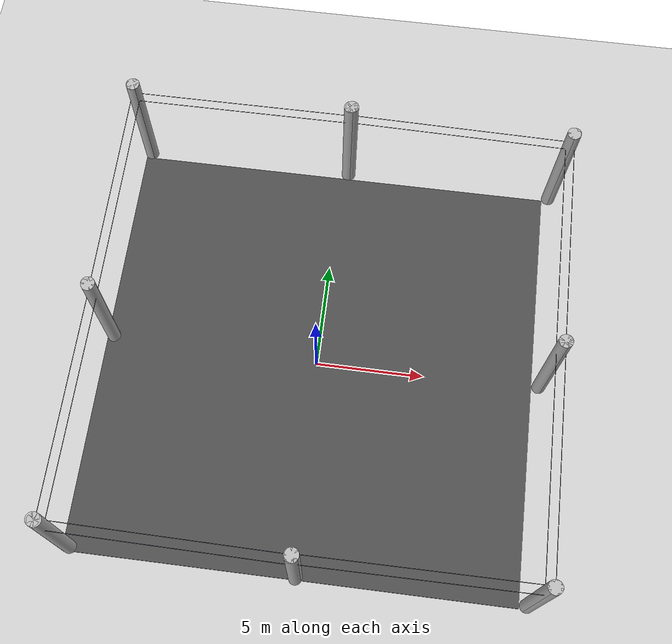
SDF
<sdf version="1.7">
 <world name="default">
  <light name="sun" type="directional">
   <pose>0 0 10 0 -0 0</pose>
   <diffuse>0.8 0.8 0.8 1</diffuse>
   <specular>0.2 0.2 0.2 1</specular>
   <attenuation>
    <range>1000</range>
    <constant>0.9</constant>
    <linear>0.01</linear>
    <quadratic>0.001</quadratic>
   </attenuation>
   <direction>-0.5 0.1 -0.9</direction>
   <spot><inner_angle>0</inner_angle><outer_angle>0</outer_angle><falloff>0</falloff></spot>
  </light>
  <model name="ground_plane">
   <static>1</static>
   <link name="link">
    <collision name="collision">
     <geometry><plane><normal>0 0 1</normal><size>100 100</size></plane></geometry>
     <surface><friction><ode><mu>100</mu><mu2>50</mu2></ode></friction></surface>
    </collision>
    <visual name="visual">
     <cast_shadows>0</cast_shadows>
     <geometry><plane><normal>0 0 1</normal><size>100 100</size></plane></geometry>
     <material>
      <script><uri>file://media/materials/scripts/gazebo.material</uri><name>Gazebo/Grey</name></script>
     </material>
    </visual>
   </link>
  </model>
  <model name="asphalt_plane">
   <pose>0.02662 0 0 0 -0 0</pose>
   <static>1</static>
   <link name="link">
    <collision name="collision"><geometry><box><size>20 20 0.1</size></box></geometry></collision>
    <visual name="visual">
     <cast_shadows>0</cast_shadows>
     <geometry><box><size>20 20 0.1</size></box></geometry>
     <material>
      <script>
       <uri>model://asphalt_plane/materials/scripts</uri>
       <uri>model://asphalt_plane/materials/textures</uri>
       <name>vrc/asphalt</name>
      </script>
     </material>
    </visual>
   </link>
  </model>
  <physics name="default_physics" default="0" type="ode">
   <ode>
    <solver>
     <type>quick</type>
     <iters>10</iters>
     <sor>1.3</sor>
     <use_dynamic_moi_rescaling>0</use_dynamic_moi_rescaling>
    </solver>
    <constraints>
     <cfm>0</cfm>
     <erp>0.2</erp>
     <contact_max_correcting_vel>100</contact_max_correcting_vel>
     <contact_surface_layer>0.001</contact_surface_layer>
    </constraints>
   </ode>
   <max_step_size>0.004</max_step_size>
   <real_time_factor>1</real_time_factor>
   <real_time_update_rate>250</real_time_update_rate>
  </physics>
  <gravity>0 0 -9.8066</gravity>
  <magnetic_field>6e-06 2.3e-05 -4.2e-05</magnetic_field>
  <atmosphere type="adiabatic"/>
  <scene><ambient>0.4 0.4 0.4 1</ambient><background>0.7 0.7 0.7 1</background><shadows>1</shadows></scene>
  <spherical_coordinates>
   <surface_model>EARTH_WGS84</surface_model>
   <latitude_deg>0</latitude_deg>
   <longitude_deg>0</longitude_deg>
   <elevation>0</elevation>
   <heading_deg>0</heading_deg>
  </spherical_coordinates>
  <model name="telegraph_pole">
   <link name="pole_00">
    <pose>0 -5 3 0 -0 0</pose>
    <inertial>
     <inertia><ixx>1</ixx><ixy>0</ixy><ixz>0</ixz><iyy>1</iyy><iyz>0</iyz><izz>1</izz></inertia>
     <mass>1</mass>
    </inertial>
    <visual name="visual">
     <geometry><cylinder><radius>0.3</radius><length>6</length></cylinder></geometry>
     <material><script><uri>__default__</uri><name>__default__</name></script></material>
    </visual>
    <collision name="collision">
     <geometry><cylinder><radius>0.3</radius><length>6</length></cylinder></geometry>
     <surface>
      <friction>
       <ode><mu>1</mu><mu2>1</mu2><fdir1>0 0 0</fdir1><slip1>0</slip1><slip2>0</slip2></ode>
       <torsional>
        <coefficient>1</coefficient>
        <patch_radius>0</patch_radius>
        <surface_radius>0</surface_radius>
        <use_patch_radius>1</use_patch_radius>
        <ode><slip>0</slip></ode>
       </torsional>
      </friction>
      <bounce><restitution_coefficient>0</restitution_coefficient><threshold>1e+06</threshold></bounce>
      <contact>
       <collide_without_contact>0</collide_without_contact>
       <collide_without_contact_bitmask>1</collide_without_contact_bitmask>
       <collide_bitmask>1</collide_bitmask>
       <ode>
        <soft_cfm>0</soft_cfm>
        <soft_erp>0.2</soft_erp>
        <kp>1e+13</kp>
        <kd>1</kd>
        <max_vel>0.01</max_vel>
        <min_depth>0</min_depth>
       </ode>
       <bullet>
        <split_impulse>1</split_impulse>
        <split_impulse_penetration_threshold>-0.01</split_impulse_penetration_threshold>
        <soft_cfm>0</soft_cfm>
        <soft_erp>0.2</soft_erp>
        <kp>1e+13</kp>
        <kd>1</kd>
       </bullet>
      </contact>
     </surface>
    </collision>
   </link>
   <link name="line00_00_01">
    <pose>-0.2 0 5 1.57 -0 0</pose>
    <inertial>
     <inertia><ixx>1</ixx><ixy>0</ixy><ixz>0</ixz><iyy>1</iyy><iyz>0</iyz><izz>1</izz></inertia>
     <mass>1</mass>
    </inertial>
    <visual name="visual">
     <geometry><cylinder><radius>0.01</radius><length>10</length></cylinder></geometry>
     <material>
      <ambient>0.1 0.1 0.1 1</ambient>
      <diffuse>0.1 0.1 0.2 1</diffuse>
      <specular>0 0 0 0</specular>
      <emissive>0 0 0 1</emissive>
      <shader type="pixel"/>
      <script><name>ModelPreview_5::line00_00_01::visual_MATERIAL_</name><uri>__default__</uri></script>
     </material>
    </visual>
    <collision name="collision">
     <geometry><cylinder><radius>0.01</radius><length>10</length></cylinder></geometry>
     <surface>
      <friction>
       <ode><mu>1</mu><mu2>1</mu2><fdir1>0 0 0</fdir1><slip1>0</slip1><slip2>0</slip2></ode>
       <torsional>
        <coefficient>1</coefficient>
        <patch_radius>0</patch_radius>
        <surface_radius>0</surface_radius>
        <use_patch_radius>1</use_patch_radius>
        <ode><slip>0</slip></ode>
       </torsional>
      </friction>
      <bounce><restitution_coefficient>0</restitution_coefficient><threshold>1e+06</threshold></bounce>
      <contact>
       <collide_without_contact>0</collide_without_contact>
       <collide_without_contact_bitmask>1</collide_without_contact_bitmask>
       <collide_bitmask>1</collide_bitmask>
       <ode>
        <soft_cfm>0</soft_cfm>
        <soft_erp>0.2</soft_erp>
        <kp>1e+13</kp>
        <kd>1</kd>
        <max_vel>0.01</max_vel>
        <min_depth>0</min_depth>
       </ode>
       <bullet>
        <split_impulse>1</split_impulse>
        <split_impulse_penetration_threshold>-0.01</split_impulse_penetration_threshold>
        <soft_cfm>0</soft_cfm>
        <soft_erp>0.2</soft_erp>
        <kp>1e+13</kp>
        <kd>1</kd>
       </bullet>
      </contact>
     </surface>
    </collision>
   </link>
   <link name="line01_00_01">
    <pose>0.2 0 5 1.57 -0 0</pose>
    <inertial>
     <inertia><ixx>1</ixx><ixy>0</ixy><ixz>0</ixz><iyy>1</iyy><iyz>0</iyz><izz>1</izz></inertia>
     <mass>1</mass>
    </inertial>
    <visual name="visual">
     <geometry><cylinder><radius>0.01</radius><length>10</length></cylinder></geometry>
     <material>
      <ambient>0.1 0.1 0.1 1</ambient>
      <diffuse>0.1 0.1 0.2 1</diffuse>
      <specular>0 0 0 0</specular>
      <emissive>0 0 0 1</emissive>
      <shader type="pixel"/>
      <script><name>ModelPreview_5::line01_00_01::visual_MATERIAL_</name><uri>__default__</uri></script>
     </material>
    </visual>
    <collision name="collision">
     <geometry><cylinder><radius>0.01</radius><length>10</length></cylinder></geometry>
     <surface>
      <friction>
       <ode><mu>1</mu><mu2>1</mu2><fdir1>0 0 0</fdir1><slip1>0</slip1><slip2>0</slip2></ode>
       <torsional>
        <coefficient>1</coefficient>
        <patch_radius>0</patch_radius>
        <surface_radius>0</surface_radius>
        <use_patch_radius>1</use_patch_radius>
        <ode><slip>0</slip></ode>
       </torsional>
      </friction>
      <bounce><restitution_coefficient>0</restitution_coefficient><threshold>1e+06</threshold></bounce>
      <contact>
       <collide_without_contact>0</collide_without_contact>
       <collide_without_contact_bitmask>1</collide_without_contact_bitmask>
       <collide_bitmask>1</collide_bitmask>
       <ode>
        <soft_cfm>0</soft_cfm>
        <soft_erp>0.2</soft_erp>
        <kp>1e+13</kp>
        <kd>1</kd>
        <max_vel>0.01</max_vel>
        <min_depth>0</min_depth>
       </ode>
       <bullet>
        <split_impulse>1</split_impulse>
        <split_impulse_penetration_threshold>-0.01</split_impulse_penetration_threshold>
        <soft_cfm>0</soft_cfm>
        <soft_erp>0.2</soft_erp>
        <kp>1e+13</kp>
        <kd>1</kd>
       </bullet>
      </contact>
     </surface>
    </collision>
   </link>
   <link name="pole_01">
    <pose>0 5 3 0 -0 0</pose>
    <inertial>
     <inertia><ixx>1</ixx><ixy>0</ixy><ixz>0</ixz><iyy>1</iyy><iyz>0</iyz><izz>1</izz></inertia>
     <mass>1</mass>
    </inertial>
    <visual name="visual">
     <geometry><cylinder><radius>0.3</radius><length>6</length></cylinder></geometry>
     <material><script><uri>__default__</uri><name>__default__</name></script></material>
    </visual>
    <collision name="collision">
     <geometry><cylinder><radius>0.3</radius><length>6</length></cylinder></geometry>
     <surface>
      <friction>
       <ode><mu>1</mu><mu2>1</mu2><fdir1>0 0 0</fdir1><slip1>0</slip1><slip2>0</slip2></ode>
       <torsional>
        <coefficient>1</coefficient>
        <patch_radius>0</patch_radius>
        <surface_radius>0</surface_radius>
        <use_patch_radius>1</use_patch_radius>
        <ode><slip>0</slip></ode>
       </torsional>
      </friction>
      <bounce><restitution_coefficient>0</restitution_coefficient><threshold>1e+06</threshold></bounce>
      <contact>
       <collide_without_contact>0</collide_without_contact>
       <collide_without_contact_bitmask>1</collide_without_contact_bitmask>
       <collide_bitmask>1</collide_bitmask>
       <ode>
        <soft_cfm>0</soft_cfm>
        <soft_erp>0.2</soft_erp>
        <kp>1e+13</kp>
        <kd>1</kd>
        <max_vel>0.01</max_vel>
        <min_depth>0</min_depth>
       </ode>
       <bullet>
        <split_impulse>1</split_impulse>
        <split_impulse_penetration_threshold>-0.01</split_impulse_penetration_threshold>
        <soft_cfm>0</soft_cfm>
        <soft_erp>0.2</soft_erp>
        <kp>1e+13</kp>
        <kd>1</kd>
       </bullet>
      </contact>
     </surface>
    </collision>
   </link>
   <joint name="line00_pole_00" type="fixed">
    <parent>pole_00</parent>
    <child>line00_00_01</child>
    <pose>0 0 5 0 -0 0</pose>
    <physics>
     <ode><limit><cfm>0</cfm><erp>0.2</erp></limit><suspension><cfm>0</cfm><erp>0.2</erp></suspension></ode>
    </physics>
   </joint>
   <joint name="line00_pole_01" type="fixed">
    <parent>pole_01</parent>
    <child>line00_00_01</child>
    <pose>0 0 -5 0 -0 0</pose>
    <physics>
     <ode><limit><cfm>0</cfm><erp>0.2</erp></limit><suspension><cfm>0</cfm><erp>0.2</erp></suspension></ode>
    </physics>
   </joint>
   <joint name="line01_pole_00" type="fixed">
    <parent>pole_00</parent>
    <child>line01_00_01</child>
    <pose>0 0 5 0 -0 0</pose>
    <physics>
     <ode><limit><cfm>0</cfm><erp>0.2</erp></limit><suspension><cfm>0</cfm><erp>0.2</erp></suspension></ode>
    </physics>
   </joint>
   <joint name="line01_pole_01" type="fixed">
    <parent>pole_01</parent>
    <child>line01_00_01</child>
    <pose>0 0 -5 0 -0 0</pose>
    <physics>
     <ode><limit><cfm>0</cfm><erp>0.2</erp></limit><suspension><cfm>0</cfm><erp>0.2</erp></suspension></ode>
    </physics>
   </joint>
   <static>1</static>
   <pose>10.374 -4.84725 0 0 -0 0</pose>
  </model>
  <model name="telegraph_pole_0">
   <link name="pole_00">
    <pose>0 -5 3 0 -0 0</pose>
    <inertial>
     <inertia><ixx>1</ixx><ixy>0</ixy><ixz>0</ixz><iyy>1</iyy><iyz>0</iyz><izz>1</izz></inertia>
     <mass>1</mass>
    </inertial>
    <visual name="visual">
     <geometry><cylinder><radius>0.3</radius><length>6</length></cylinder></geometry>
     <material><script><uri>__default__</uri><name>__default__</name></script></material>
    </visual>
    <collision name="collision">
     <geometry><cylinder><radius>0.3</radius><length>6</length></cylinder></geometry>
     <surface>
      <friction>
       <ode><mu>1</mu><mu2>1</mu2><fdir1>0 0 0</fdir1><slip1>0</slip1><slip2>0</slip2></ode>
       <torsional>
        <coefficient>1</coefficient>
        <patch_radius>0</patch_radius>
        <surface_radius>0</surface_radius>
        <use_patch_radius>1</use_patch_radius>
        <ode><slip>0</slip></ode>
       </torsional>
      </friction>
      <bounce><restitution_coefficient>0</restitution_coefficient><threshold>1e+06</threshold></bounce>
      <contact>
       <collide_without_contact>0</collide_without_contact>
       <collide_without_contact_bitmask>1</collide_without_contact_bitmask>
       <collide_bitmask>1</collide_bitmask>
       <ode>
        <soft_cfm>0</soft_cfm>
        <soft_erp>0.2</soft_erp>
        <kp>1e+13</kp>
        <kd>1</kd>
        <max_vel>0.01</max_vel>
        <min_depth>0</min_depth>
       </ode>
       <bullet>
        <split_impulse>1</split_impulse>
        <split_impulse_penetration_threshold>-0.01</split_impulse_penetration_threshold>
        <soft_cfm>0</soft_cfm>
        <soft_erp>0.2</soft_erp>
        <kp>1e+13</kp>
        <kd>1</kd>
       </bullet>
      </contact>
     </surface>
    </collision>
   </link>
   <link name="line00_00_01">
    <pose>-0.2 0 5 1.57 -0 0</pose>
    <inertial>
     <inertia><ixx>1</ixx><ixy>0</ixy><ixz>0</ixz><iyy>1</iyy><iyz>0</iyz><izz>1</izz></inertia>
     <mass>1</mass>
    </inertial>
    <visual name="visual">
     <geometry><cylinder><radius>0.01</radius><length>10</length></cylinder></geometry>
     <material>
      <ambient>0.1 0.1 0.1 1</ambient>
      <diffuse>0.1 0.1 0.2 1</diffuse>
      <specular>0 0 0 0</specular>
      <emissive>0 0 0 1</emissive>
      <shader type="pixel"/>
      <script><name>ModelPreview_5::line00_00_01::visual_MATERIAL_</name><uri>__default__</uri></script>
     </material>
    </visual>
    <collision name="collision">
     <geometry><cylinder><radius>0.01</radius><length>10</length></cylinder></geometry>
     <surface>
      <friction>
       <ode><mu>1</mu><mu2>1</mu2><fdir1>0 0 0</fdir1><slip1>0</slip1><slip2>0</slip2></ode>
       <torsional>
        <coefficient>1</coefficient>
        <patch_radius>0</patch_radius>
        <surface_radius>0</surface_radius>
        <use_patch_radius>1</use_patch_radius>
        <ode><slip>0</slip></ode>
       </torsional>
      </friction>
      <bounce><restitution_coefficient>0</restitution_coefficient><threshold>1e+06</threshold></bounce>
      <contact>
       <collide_without_contact>0</collide_without_contact>
       <collide_without_contact_bitmask>1</collide_without_contact_bitmask>
       <collide_bitmask>1</collide_bitmask>
       <ode>
        <soft_cfm>0</soft_cfm>
        <soft_erp>0.2</soft_erp>
        <kp>1e+13</kp>
        <kd>1</kd>
        <max_vel>0.01</max_vel>
        <min_depth>0</min_depth>
       </ode>
       <bullet>
        <split_impulse>1</split_impulse>
        <split_impulse_penetration_threshold>-0.01</split_impulse_penetration_threshold>
        <soft_cfm>0</soft_cfm>
        <soft_erp>0.2</soft_erp>
        <kp>1e+13</kp>
        <kd>1</kd>
       </bullet>
      </contact>
     </surface>
    </collision>
   </link>
   <link name="line01_00_01">
    <pose>0.2 0 5 1.57 -0 0</pose>
    <inertial>
     <inertia><ixx>1</ixx><ixy>0</ixy><ixz>0</ixz><iyy>1</iyy><iyz>0</iyz><izz>1</izz></inertia>
     <mass>1</mass>
    </inertial>
    <visual name="visual">
     <geometry><cylinder><radius>0.01</radius><length>10</length></cylinder></geometry>
     <material>
      <ambient>0.1 0.1 0.1 1</ambient>
      <diffuse>0.1 0.1 0.2 1</diffuse>
      <specular>0 0 0 0</specular>
      <emissive>0 0 0 1</emissive>
      <shader type="pixel"/>
      <script><name>ModelPreview_5::line01_00_01::visual_MATERIAL_</name><uri>__default__</uri></script>
     </material>
    </visual>
    <collision name="collision">
     <geometry><cylinder><radius>0.01</radius><length>10</length></cylinder></geometry>
     <surface>
      <friction>
       <ode><mu>1</mu><mu2>1</mu2><fdir1>0 0 0</fdir1><slip1>0</slip1><slip2>0</slip2></ode>
       <torsional>
        <coefficient>1</coefficient>
        <patch_radius>0</patch_radius>
        <surface_radius>0</surface_radius>
        <use_patch_radius>1</use_patch_radius>
        <ode><slip>0</slip></ode>
       </torsional>
      </friction>
      <bounce><restitution_coefficient>0</restitution_coefficient><threshold>1e+06</threshold></bounce>
      <contact>
       <collide_without_contact>0</collide_without_contact>
       <collide_without_contact_bitmask>1</collide_without_contact_bitmask>
       <collide_bitmask>1</collide_bitmask>
       <ode>
        <soft_cfm>0</soft_cfm>
        <soft_erp>0.2</soft_erp>
        <kp>1e+13</kp>
        <kd>1</kd>
        <max_vel>0.01</max_vel>
        <min_depth>0</min_depth>
       </ode>
       <bullet>
        <split_impulse>1</split_impulse>
        <split_impulse_penetration_threshold>-0.01</split_impulse_penetration_threshold>
        <soft_cfm>0</soft_cfm>
        <soft_erp>0.2</soft_erp>
        <kp>1e+13</kp>
        <kd>1</kd>
       </bullet>
      </contact>
     </surface>
    </collision>
   </link>
   <link name="pole_01">
    <pose>0 5 3 0 -0 0</pose>
    <inertial>
     <inertia><ixx>1</ixx><ixy>0</ixy><ixz>0</ixz><iyy>1</iyy><iyz>0</iyz><izz>1</izz></inertia>
     <mass>1</mass>
    </inertial>
    <visual name="visual">
     <geometry><cylinder><radius>0.3</radius><length>6</length></cylinder></geometry>
     <material><script><uri>__default__</uri><name>__default__</name></script></material>
    </visual>
    <collision name="collision">
     <geometry><cylinder><radius>0.3</radius><length>6</length></cylinder></geometry>
     <surface>
      <friction>
       <ode><mu>1</mu><mu2>1</mu2><fdir1>0 0 0</fdir1><slip1>0</slip1><slip2>0</slip2></ode>
       <torsional>
        <coefficient>1</coefficient>
        <patch_radius>0</patch_radius>
        <surface_radius>0</surface_radius>
        <use_patch_radius>1</use_patch_radius>
        <ode><slip>0</slip></ode>
       </torsional>
      </friction>
      <bounce><restitution_coefficient>0</restitution_coefficient><threshold>1e+06</threshold></bounce>
      <contact>
       <collide_without_contact>0</collide_without_contact>
       <collide_without_contact_bitmask>1</collide_without_contact_bitmask>
       <collide_bitmask>1</collide_bitmask>
       <ode>
        <soft_cfm>0</soft_cfm>
        <soft_erp>0.2</soft_erp>
        <kp>1e+13</kp>
        <kd>1</kd>
        <max_vel>0.01</max_vel>
        <min_depth>0</min_depth>
       </ode>
       <bullet>
        <split_impulse>1</split_impulse>
        <split_impulse_penetration_threshold>-0.01</split_impulse_penetration_threshold>
        <soft_cfm>0</soft_cfm>
        <soft_erp>0.2</soft_erp>
        <kp>1e+13</kp>
        <kd>1</kd>
       </bullet>
      </contact>
     </surface>
    </collision>
   </link>
   <joint name="line00_pole_00" type="fixed">
    <parent>pole_00</parent>
    <child>line00_00_01</child>
    <pose>0 0 5 0 -0 0</pose>
    <physics>
     <ode><limit><cfm>0</cfm><erp>0.2</erp></limit><suspension><cfm>0</cfm><erp>0.2</erp></suspension></ode>
    </physics>
   </joint>
   <joint name="line00_pole_01" type="fixed">
    <parent>pole_01</parent>
    <child>line00_00_01</child>
    <pose>0 0 -5 0 -0 0</pose>
    <physics>
     <ode><limit><cfm>0</cfm><erp>0.2</erp></limit><suspension><cfm>0</cfm><erp>0.2</erp></suspension></ode>
    </physics>
   </joint>
   <joint name="line01_pole_00" type="fixed">
    <parent>pole_00</parent>
    <child>line01_00_01</child>
    <pose>0 0 5 0 -0 0</pose>
    <physics>
     <ode><limit><cfm>0</cfm><erp>0.2</erp></limit><suspension><cfm>0</cfm><erp>0.2</erp></suspension></ode>
    </physics>
   </joint>
   <joint name="line01_pole_01" type="fixed">
    <parent>pole_01</parent>
    <child>line01_00_01</child>
    <pose>0 0 -5 0 -0 0</pose>
    <physics>
     <ode><limit><cfm>0</cfm><erp>0.2</erp></limit><suspension><cfm>0</cfm><erp>0.2</erp></suspension></ode>
    </physics>
   </joint>
   <static>1</static>
   <pose>-9.70943 -4.78365 0 0 0 -0.003814</pose>
  </model>
  <model name="telegraph_pole_0_clone">
   <link name="pole_00">
    <pose>0 -5 3 0 -0 0</pose>
    <inertial>
     <inertia><ixx>1</ixx><ixy>0</ixy><ixz>0</ixz><iyy>1</iyy><iyz>0</iyz><izz>1</izz></inertia>
     <mass>1</mass>
    </inertial>
    <visual name="visual">
     <geometry><cylinder><radius>0.3</radius><length>6</length></cylinder></geometry>
     <material><script><uri>__default__</uri><name>__default__</name></script></material>
    </visual>
    <collision name="collision">
     <geometry><cylinder><radius>0.3</radius><length>6</length></cylinder></geometry>
     <surface>
      <friction>
       <ode><mu>1</mu><mu2>1</mu2><fdir1>0 0 0</fdir1><slip1>0</slip1><slip2>0</slip2></ode>
       <torsional>
        <coefficient>1</coefficient>
        <patch_radius>0</patch_radius>
        <surface_radius>0</surface_radius>
        <use_patch_radius>1</use_patch_radius>
        <ode><slip>0</slip></ode>
       </torsional>
      </friction>
      <bounce><restitution_coefficient>0</restitution_coefficient><threshold>1e+06</threshold></bounce>
      <contact>
       <collide_without_contact>0</collide_without_contact>
       <collide_without_contact_bitmask>1</collide_without_contact_bitmask>
       <collide_bitmask>1</collide_bitmask>
       <ode>
        <soft_cfm>0</soft_cfm>
        <soft_erp>0.2</soft_erp>
        <kp>1e+13</kp>
        <kd>1</kd>
        <max_vel>0.01</max_vel>
        <min_depth>0</min_depth>
       </ode>
       <bullet>
        <split_impulse>1</split_impulse>
        <split_impulse_penetration_threshold>-0.01</split_impulse_penetration_threshold>
        <soft_cfm>0</soft_cfm>
        <soft_erp>0.2</soft_erp>
        <kp>1e+13</kp>
        <kd>1</kd>
       </bullet>
      </contact>
     </surface>
    </collision>
   </link>
   <link name="line00_00_01">
    <pose>-0.2 0 5 1.57 -0 0</pose>
    <inertial>
     <inertia><ixx>1</ixx><ixy>0</ixy><ixz>0</ixz><iyy>1</iyy><iyz>0</iyz><izz>1</izz></inertia>
     <mass>1</mass>
    </inertial>
    <visual name="visual">
     <geometry><cylinder><radius>0.01</radius><length>10</length></cylinder></geometry>
     <material>
      <ambient>0.1 0.1 0.1 1</ambient>
      <diffuse>0.1 0.1 0.2 1</diffuse>
      <specular>0 0 0 0</specular>
      <emissive>0 0 0 1</emissive>
      <shader type="pixel"/>
      <script><name>ModelPreview_5::line00_00_01::visual_MATERIAL_</name><uri>__default__</uri></script>
     </material>
    </visual>
    <collision name="collision">
     <geometry><cylinder><radius>0.01</radius><length>10</length></cylinder></geometry>
     <surface>
      <friction>
       <ode><mu>1</mu><mu2>1</mu2><fdir1>0 0 0</fdir1><slip1>0</slip1><slip2>0</slip2></ode>
       <torsional>
        <coefficient>1</coefficient>
        <patch_radius>0</patch_radius>
        <surface_radius>0</surface_radius>
        <use_patch_radius>1</use_patch_radius>
        <ode><slip>0</slip></ode>
       </torsional>
      </friction>
      <bounce><restitution_coefficient>0</restitution_coefficient><threshold>1e+06</threshold></bounce>
      <contact>
       <collide_without_contact>0</collide_without_contact>
       <collide_without_contact_bitmask>1</collide_without_contact_bitmask>
       <collide_bitmask>1</collide_bitmask>
       <ode>
        <soft_cfm>0</soft_cfm>
        <soft_erp>0.2</soft_erp>
        <kp>1e+13</kp>
        <kd>1</kd>
        <max_vel>0.01</max_vel>
        <min_depth>0</min_depth>
       </ode>
       <bullet>
        <split_impulse>1</split_impulse>
        <split_impulse_penetration_threshold>-0.01</split_impulse_penetration_threshold>
        <soft_cfm>0</soft_cfm>
        <soft_erp>0.2</soft_erp>
        <kp>1e+13</kp>
        <kd>1</kd>
       </bullet>
      </contact>
     </surface>
    </collision>
   </link>
   <link name="line01_00_01">
    <pose>0.2 0 5 1.57 -0 0</pose>
    <inertial>
     <inertia><ixx>1</ixx><ixy>0</ixy><ixz>0</ixz><iyy>1</iyy><iyz>0</iyz><izz>1</izz></inertia>
     <mass>1</mass>
    </inertial>
    <visual name="visual">
     <geometry><cylinder><radius>0.01</radius><length>10</length></cylinder></geometry>
     <material>
      <ambient>0.1 0.1 0.1 1</ambient>
      <diffuse>0.1 0.1 0.2 1</diffuse>
      <specular>0 0 0 0</specular>
      <emissive>0 0 0 1</emissive>
      <shader type="pixel"/>
      <script><name>ModelPreview_5::line01_00_01::visual_MATERIAL_</name><uri>__default__</uri></script>
     </material>
    </visual>
    <collision name="collision">
     <geometry><cylinder><radius>0.01</radius><length>10</length></cylinder></geometry>
     <surface>
      <friction>
       <ode><mu>1</mu><mu2>1</mu2><fdir1>0 0 0</fdir1><slip1>0</slip1><slip2>0</slip2></ode>
       <torsional>
        <coefficient>1</coefficient>
        <patch_radius>0</patch_radius>
        <surface_radius>0</surface_radius>
        <use_patch_radius>1</use_patch_radius>
        <ode><slip>0</slip></ode>
       </torsional>
      </friction>
      <bounce><restitution_coefficient>0</restitution_coefficient><threshold>1e+06</threshold></bounce>
      <contact>
       <collide_without_contact>0</collide_without_contact>
       <collide_without_contact_bitmask>1</collide_without_contact_bitmask>
       <collide_bitmask>1</collide_bitmask>
       <ode>
        <soft_cfm>0</soft_cfm>
        <soft_erp>0.2</soft_erp>
        <kp>1e+13</kp>
        <kd>1</kd>
        <max_vel>0.01</max_vel>
        <min_depth>0</min_depth>
       </ode>
       <bullet>
        <split_impulse>1</split_impulse>
        <split_impulse_penetration_threshold>-0.01</split_impulse_penetration_threshold>
        <soft_cfm>0</soft_cfm>
        <soft_erp>0.2</soft_erp>
        <kp>1e+13</kp>
        <kd>1</kd>
       </bullet>
      </contact>
     </surface>
    </collision>
   </link>
   <link name="pole_01">
    <pose>0 5 3 0 -0 0</pose>
    <inertial>
     <inertia><ixx>1</ixx><ixy>0</ixy><ixz>0</ixz><iyy>1</iyy><iyz>0</iyz><izz>1</izz></inertia>
     <mass>1</mass>
    </inertial>
    <visual name="visual">
     <geometry><cylinder><radius>0.3</radius><length>6</length></cylinder></geometry>
     <material><script><uri>__default__</uri><name>__default__</name></script></material>
    </visual>
    <collision name="collision">
     <geometry><cylinder><radius>0.3</radius><length>6</length></cylinder></geometry>
     <surface>
      <friction>
       <ode><mu>1</mu><mu2>1</mu2><fdir1>0 0 0</fdir1><slip1>0</slip1><slip2>0</slip2></ode>
       <torsional>
        <coefficient>1</coefficient>
        <patch_radius>0</patch_radius>
        <surface_radius>0</surface_radius>
        <use_patch_radius>1</use_patch_radius>
        <ode><slip>0</slip></ode>
       </torsional>
      </friction>
      <bounce><restitution_coefficient>0</restitution_coefficient><threshold>1e+06</threshold></bounce>
      <contact>
       <collide_without_contact>0</collide_without_contact>
       <collide_without_contact_bitmask>1</collide_without_contact_bitmask>
       <collide_bitmask>1</collide_bitmask>
       <ode>
        <soft_cfm>0</soft_cfm>
        <soft_erp>0.2</soft_erp>
        <kp>1e+13</kp>
        <kd>1</kd>
        <max_vel>0.01</max_vel>
        <min_depth>0</min_depth>
       </ode>
       <bullet>
        <split_impulse>1</split_impulse>
        <split_impulse_penetration_threshold>-0.01</split_impulse_penetration_threshold>
        <soft_cfm>0</soft_cfm>
        <soft_erp>0.2</soft_erp>
        <kp>1e+13</kp>
        <kd>1</kd>
       </bullet>
      </contact>
     </surface>
    </collision>
   </link>
   <joint name="line00_pole_00" type="fixed">
    <parent>pole_00</parent>
    <child>line00_00_01</child>
    <pose>0 0 5 0 -0 0</pose>
    <physics>
     <ode><limit><cfm>0</cfm><erp>0.2</erp></limit><suspension><cfm>0</cfm><erp>0.2</erp></suspension></ode>
    </physics>
   </joint>
   <joint name="line00_pole_01" type="fixed">
    <parent>pole_01</parent>
    <child>line00_00_01</child>
    <pose>0 0 -5 0 -0 0</pose>
    <physics>
     <ode><limit><cfm>0</cfm><erp>0.2</erp></limit><suspension><cfm>0</cfm><erp>0.2</erp></suspension></ode>
    </physics>
   </joint>
   <joint name="line01_pole_00" type="fixed">
    <parent>pole_00</parent>
    <child>line01_00_01</child>
    <pose>0 0 5 0 -0 0</pose>
    <physics>
     <ode><limit><cfm>0</cfm><erp>0.2</erp></limit><suspension><cfm>0</cfm><erp>0.2</erp></suspension></ode>
    </physics>
   </joint>
   <joint name="line01_pole_01" type="fixed">
    <parent>pole_01</parent>
    <child>line01_00_01</child>
    <pose>0 0 -5 0 -0 0</pose>
    <physics>
     <ode><limit><cfm>0</cfm><erp>0.2</erp></limit><suspension><cfm>0</cfm><erp>0.2</erp></suspension></ode>
    </physics>
   </joint>
   <static>1</static>
   <pose>-9.72507 5.25235 0 0 -0 0.004262</pose>
  </model>
  <model name="telegraph_pole_0_clone_0">
   <link name="pole_00">
    <pose>0 -5 3 0 -0 0</pose>
    <inertial>
     <inertia><ixx>1</ixx><ixy>0</ixy><ixz>0</ixz><iyy>1</iyy><iyz>0</iyz><izz>1</izz></inertia>
     <mass>1</mass>
    </inertial>
    <visual name="visual">
     <geometry><cylinder><radius>0.3</radius><length>6</length></cylinder></geometry>
     <material><script><uri>__default__</uri><name>__default__</name></script></material>
    </visual>
    <collision name="collision">
     <geometry><cylinder><radius>0.3</radius><length>6</length></cylinder></geometry>
     <surface>
      <friction>
       <ode><mu>1</mu><mu2>1</mu2><fdir1>0 0 0</fdir1><slip1>0</slip1><slip2>0</slip2></ode>
       <torsional>
        <coefficient>1</coefficient>
        <patch_radius>0</patch_radius>
        <surface_radius>0</surface_radius>
        <use_patch_radius>1</use_patch_radius>
        <ode><slip>0</slip></ode>
       </torsional>
      </friction>
      <bounce><restitution_coefficient>0</restitution_coefficient><threshold>1e+06</threshold></bounce>
      <contact>
       <collide_without_contact>0</collide_without_contact>
       <collide_without_contact_bitmask>1</collide_without_contact_bitmask>
       <collide_bitmask>1</collide_bitmask>
       <ode>
        <soft_cfm>0</soft_cfm>
        <soft_erp>0.2</soft_erp>
        <kp>1e+13</kp>
        <kd>1</kd>
        <max_vel>0.01</max_vel>
        <min_depth>0</min_depth>
       </ode>
       <bullet>
        <split_impulse>1</split_impulse>
        <split_impulse_penetration_threshold>-0.01</split_impulse_penetration_threshold>
        <soft_cfm>0</soft_cfm>
        <soft_erp>0.2</soft_erp>
        <kp>1e+13</kp>
        <kd>1</kd>
       </bullet>
      </contact>
     </surface>
    </collision>
   </link>
   <link name="line00_00_01">
    <pose>-0.2 0 5 1.57 -0 0</pose>
    <inertial>
     <inertia><ixx>1</ixx><ixy>0</ixy><ixz>0</ixz><iyy>1</iyy><iyz>0</iyz><izz>1</izz></inertia>
     <mass>1</mass>
    </inertial>
    <visual name="visual">
     <geometry><cylinder><radius>0.01</radius><length>10</length></cylinder></geometry>
     <material>
      <ambient>0.1 0.1 0.1 1</ambient>
      <diffuse>0.1 0.1 0.2 1</diffuse>
      <specular>0 0 0 0</specular>
      <emissive>0 0 0 1</emissive>
      <shader type="pixel"/>
      <script><name>ModelPreview_5::line00_00_01::visual_MATERIAL_</name><uri>__default__</uri></script>
     </material>
    </visual>
    <collision name="collision">
     <geometry><cylinder><radius>0.01</radius><length>10</length></cylinder></geometry>
     <surface>
      <friction>
       <ode><mu>1</mu><mu2>1</mu2><fdir1>0 0 0</fdir1><slip1>0</slip1><slip2>0</slip2></ode>
       <torsional>
        <coefficient>1</coefficient>
        <patch_radius>0</patch_radius>
        <surface_radius>0</surface_radius>
        <use_patch_radius>1</use_patch_radius>
        <ode><slip>0</slip></ode>
       </torsional>
      </friction>
      <bounce><restitution_coefficient>0</restitution_coefficient><threshold>1e+06</threshold></bounce>
      <contact>
       <collide_without_contact>0</collide_without_contact>
       <collide_without_contact_bitmask>1</collide_without_contact_bitmask>
       <collide_bitmask>1</collide_bitmask>
       <ode>
        <soft_cfm>0</soft_cfm>
        <soft_erp>0.2</soft_erp>
        <kp>1e+13</kp>
        <kd>1</kd>
        <max_vel>0.01</max_vel>
        <min_depth>0</min_depth>
       </ode>
       <bullet>
        <split_impulse>1</split_impulse>
        <split_impulse_penetration_threshold>-0.01</split_impulse_penetration_threshold>
        <soft_cfm>0</soft_cfm>
        <soft_erp>0.2</soft_erp>
        <kp>1e+13</kp>
        <kd>1</kd>
       </bullet>
      </contact>
     </surface>
    </collision>
   </link>
   <link name="line01_00_01">
    <pose>0.2 0 5 1.57 -0 0</pose>
    <inertial>
     <inertia><ixx>1</ixx><ixy>0</ixy><ixz>0</ixz><iyy>1</iyy><iyz>0</iyz><izz>1</izz></inertia>
     <mass>1</mass>
    </inertial>
    <visual name="visual">
     <geometry><cylinder><radius>0.01</radius><length>10</length></cylinder></geometry>
     <material>
      <ambient>0.1 0.1 0.1 1</ambient>
      <diffuse>0.1 0.1 0.2 1</diffuse>
      <specular>0 0 0 0</specular>
      <emissive>0 0 0 1</emissive>
      <shader type="pixel"/>
      <script><name>ModelPreview_5::line01_00_01::visual_MATERIAL_</name><uri>__default__</uri></script>
     </material>
    </visual>
    <collision name="collision">
     <geometry><cylinder><radius>0.01</radius><length>10</length></cylinder></geometry>
     <surface>
      <friction>
       <ode><mu>1</mu><mu2>1</mu2><fdir1>0 0 0</fdir1><slip1>0</slip1><slip2>0</slip2></ode>
       <torsional>
        <coefficient>1</coefficient>
        <patch_radius>0</patch_radius>
        <surface_radius>0</surface_radius>
        <use_patch_radius>1</use_patch_radius>
        <ode><slip>0</slip></ode>
       </torsional>
      </friction>
      <bounce><restitution_coefficient>0</restitution_coefficient><threshold>1e+06</threshold></bounce>
      <contact>
       <collide_without_contact>0</collide_without_contact>
       <collide_without_contact_bitmask>1</collide_without_contact_bitmask>
       <collide_bitmask>1</collide_bitmask>
       <ode>
        <soft_cfm>0</soft_cfm>
        <soft_erp>0.2</soft_erp>
        <kp>1e+13</kp>
        <kd>1</kd>
        <max_vel>0.01</max_vel>
        <min_depth>0</min_depth>
       </ode>
       <bullet>
        <split_impulse>1</split_impulse>
        <split_impulse_penetration_threshold>-0.01</split_impulse_penetration_threshold>
        <soft_cfm>0</soft_cfm>
        <soft_erp>0.2</soft_erp>
        <kp>1e+13</kp>
        <kd>1</kd>
       </bullet>
      </contact>
     </surface>
    </collision>
   </link>
   <link name="pole_01">
    <pose>0 5 3 0 -0 0</pose>
    <inertial>
     <inertia><ixx>1</ixx><ixy>0</ixy><ixz>0</ixz><iyy>1</iyy><iyz>0</iyz><izz>1</izz></inertia>
     <mass>1</mass>
    </inertial>
    <visual name="visual">
     <geometry><cylinder><radius>0.3</radius><length>6</length></cylinder></geometry>
     <material><script><uri>__default__</uri><name>__default__</name></script></material>
    </visual>
    <collision name="collision">
     <geometry><cylinder><radius>0.3</radius><length>6</length></cylinder></geometry>
     <surface>
      <friction>
       <ode><mu>1</mu><mu2>1</mu2><fdir1>0 0 0</fdir1><slip1>0</slip1><slip2>0</slip2></ode>
       <torsional>
        <coefficient>1</coefficient>
        <patch_radius>0</patch_radius>
        <surface_radius>0</surface_radius>
        <use_patch_radius>1</use_patch_radius>
        <ode><slip>0</slip></ode>
       </torsional>
      </friction>
      <bounce><restitution_coefficient>0</restitution_coefficient><threshold>1e+06</threshold></bounce>
      <contact>
       <collide_without_contact>0</collide_without_contact>
       <collide_without_contact_bitmask>1</collide_without_contact_bitmask>
       <collide_bitmask>1</collide_bitmask>
       <ode>
        <soft_cfm>0</soft_cfm>
        <soft_erp>0.2</soft_erp>
        <kp>1e+13</kp>
        <kd>1</kd>
        <max_vel>0.01</max_vel>
        <min_depth>0</min_depth>
       </ode>
       <bullet>
        <split_impulse>1</split_impulse>
        <split_impulse_penetration_threshold>-0.01</split_impulse_penetration_threshold>
        <soft_cfm>0</soft_cfm>
        <soft_erp>0.2</soft_erp>
        <kp>1e+13</kp>
        <kd>1</kd>
       </bullet>
      </contact>
     </surface>
    </collision>
   </link>
   <joint name="line00_pole_00" type="fixed">
    <parent>pole_00</parent>
    <child>line00_00_01</child>
    <pose>0 0 5 0 -0 0</pose>
    <physics>
     <ode><limit><cfm>0</cfm><erp>0.2</erp></limit><suspension><cfm>0</cfm><erp>0.2</erp></suspension></ode>
    </physics>
   </joint>
   <joint name="line00_pole_01" type="fixed">
    <parent>pole_01</parent>
    <child>line00_00_01</child>
    <pose>0 0 -5 0 -0 0</pose>
    <physics>
     <ode><limit><cfm>0</cfm><erp>0.2</erp></limit><suspension><cfm>0</cfm><erp>0.2</erp></suspension></ode>
    </physics>
   </joint>
   <joint name="line01_pole_00" type="fixed">
    <parent>pole_00</parent>
    <child>line01_00_01</child>
    <pose>0 0 5 0 -0 0</pose>
    <physics>
     <ode><limit><cfm>0</cfm><erp>0.2</erp></limit><suspension><cfm>0</cfm><erp>0.2</erp></suspension></ode>
    </physics>
   </joint>
   <joint name="line01_pole_01" type="fixed">
    <parent>pole_01</parent>
    <child>line01_00_01</child>
    <pose>0 0 -5 0 -0 0</pose>
    <physics>
     <ode><limit><cfm>0</cfm><erp>0.2</erp></limit><suspension><cfm>0</cfm><erp>0.2</erp></suspension></ode>
    </physics>
   </joint>
   <static>1</static>
   <pose>5.35625 -9.86121 0 0 0 -1.56607</pose>
  </model>
  <model name="telegraph_pole_0_clone_1">
   <link name="pole_00">
    <pose>0 -5 3 0 -0 0</pose>
    <inertial>
     <inertia><ixx>1</ixx><ixy>0</ixy><ixz>0</ixz><iyy>1</iyy><iyz>0</iyz><izz>1</izz></inertia>
     <mass>1</mass>
    </inertial>
    <visual name="visual">
     <geometry><cylinder><radius>0.3</radius><length>6</length></cylinder></geometry>
     <material><script><uri>__default__</uri><name>__default__</name></script></material>
    </visual>
    <collision name="collision">
     <geometry><cylinder><radius>0.3</radius><length>6</length></cylinder></geometry>
     <surface>
      <friction>
       <ode><mu>1</mu><mu2>1</mu2><fdir1>0 0 0</fdir1><slip1>0</slip1><slip2>0</slip2></ode>
       <torsional>
        <coefficient>1</coefficient>
        <patch_radius>0</patch_radius>
        <surface_radius>0</surface_radius>
        <use_patch_radius>1</use_patch_radius>
        <ode><slip>0</slip></ode>
       </torsional>
      </friction>
      <bounce><restitution_coefficient>0</restitution_coefficient><threshold>1e+06</threshold></bounce>
      <contact>
       <collide_without_contact>0</collide_without_contact>
       <collide_without_contact_bitmask>1</collide_without_contact_bitmask>
       <collide_bitmask>1</collide_bitmask>
       <ode>
        <soft_cfm>0</soft_cfm>
        <soft_erp>0.2</soft_erp>
        <kp>1e+13</kp>
        <kd>1</kd>
        <max_vel>0.01</max_vel>
        <min_depth>0</min_depth>
       </ode>
       <bullet>
        <split_impulse>1</split_impulse>
        <split_impulse_penetration_threshold>-0.01</split_impulse_penetration_threshold>
        <soft_cfm>0</soft_cfm>
        <soft_erp>0.2</soft_erp>
        <kp>1e+13</kp>
        <kd>1</kd>
       </bullet>
      </contact>
     </surface>
    </collision>
   </link>
   <link name="line00_00_01">
    <pose>-0.2 0 5 1.57 -0 0</pose>
    <inertial>
     <inertia><ixx>1</ixx><ixy>0</ixy><ixz>0</ixz><iyy>1</iyy><iyz>0</iyz><izz>1</izz></inertia>
     <mass>1</mass>
    </inertial>
    <visual name="visual">
     <geometry><cylinder><radius>0.01</radius><length>10</length></cylinder></geometry>
     <material>
      <ambient>0.1 0.1 0.1 1</ambient>
      <diffuse>0.1 0.1 0.2 1</diffuse>
      <specular>0 0 0 0</specular>
      <emissive>0 0 0 1</emissive>
      <shader type="pixel"/>
      <script><name>ModelPreview_5::line00_00_01::visual_MATERIAL_</name><uri>__default__</uri></script>
     </material>
    </visual>
    <collision name="collision">
     <geometry><cylinder><radius>0.01</radius><length>10</length></cylinder></geometry>
     <surface>
      <friction>
       <ode><mu>1</mu><mu2>1</mu2><fdir1>0 0 0</fdir1><slip1>0</slip1><slip2>0</slip2></ode>
       <torsional>
        <coefficient>1</coefficient>
        <patch_radius>0</patch_radius>
        <surface_radius>0</surface_radius>
        <use_patch_radius>1</use_patch_radius>
        <ode><slip>0</slip></ode>
       </torsional>
      </friction>
      <bounce><restitution_coefficient>0</restitution_coefficient><threshold>1e+06</threshold></bounce>
      <contact>
       <collide_without_contact>0</collide_without_contact>
       <collide_without_contact_bitmask>1</collide_without_contact_bitmask>
       <collide_bitmask>1</collide_bitmask>
       <ode>
        <soft_cfm>0</soft_cfm>
        <soft_erp>0.2</soft_erp>
        <kp>1e+13</kp>
        <kd>1</kd>
        <max_vel>0.01</max_vel>
        <min_depth>0</min_depth>
       </ode>
       <bullet>
        <split_impulse>1</split_impulse>
        <split_impulse_penetration_threshold>-0.01</split_impulse_penetration_threshold>
        <soft_cfm>0</soft_cfm>
        <soft_erp>0.2</soft_erp>
        <kp>1e+13</kp>
        <kd>1</kd>
       </bullet>
      </contact>
     </surface>
    </collision>
   </link>
   <link name="line01_00_01">
    <pose>0.2 0 5 1.57 -0 0</pose>
    <inertial>
     <inertia><ixx>1</ixx><ixy>0</ixy><ixz>0</ixz><iyy>1</iyy><iyz>0</iyz><izz>1</izz></inertia>
     <mass>1</mass>
    </inertial>
    <visual name="visual">
     <geometry><cylinder><radius>0.01</radius><length>10</length></cylinder></geometry>
     <material>
      <ambient>0.1 0.1 0.1 1</ambient>
      <diffuse>0.1 0.1 0.2 1</diffuse>
      <specular>0 0 0 0</specular>
      <emissive>0 0 0 1</emissive>
      <shader type="pixel"/>
      <script><name>ModelPreview_5::line01_00_01::visual_MATERIAL_</name><uri>__default__</uri></script>
     </material>
    </visual>
    <collision name="collision">
     <geometry><cylinder><radius>0.01</radius><length>10</length></cylinder></geometry>
     <surface>
      <friction>
       <ode><mu>1</mu><mu2>1</mu2><fdir1>0 0 0</fdir1><slip1>0</slip1><slip2>0</slip2></ode>
       <torsional>
        <coefficient>1</coefficient>
        <patch_radius>0</patch_radius>
        <surface_radius>0</surface_radius>
        <use_patch_radius>1</use_patch_radius>
        <ode><slip>0</slip></ode>
       </torsional>
      </friction>
      <bounce><restitution_coefficient>0</restitution_coefficient><threshold>1e+06</threshold></bounce>
      <contact>
       <collide_without_contact>0</collide_without_contact>
       <collide_without_contact_bitmask>1</collide_without_contact_bitmask>
       <collide_bitmask>1</collide_bitmask>
       <ode>
        <soft_cfm>0</soft_cfm>
        <soft_erp>0.2</soft_erp>
        <kp>1e+13</kp>
        <kd>1</kd>
        <max_vel>0.01</max_vel>
        <min_depth>0</min_depth>
       </ode>
       <bullet>
        <split_impulse>1</split_impulse>
        <split_impulse_penetration_threshold>-0.01</split_impulse_penetration_threshold>
        <soft_cfm>0</soft_cfm>
        <soft_erp>0.2</soft_erp>
        <kp>1e+13</kp>
        <kd>1</kd>
       </bullet>
      </contact>
     </surface>
    </collision>
   </link>
   <link name="pole_01">
    <pose>0 5 3 0 -0 0</pose>
    <inertial>
     <inertia><ixx>1</ixx><ixy>0</ixy><ixz>0</ixz><iyy>1</iyy><iyz>0</iyz><izz>1</izz></inertia>
     <mass>1</mass>
    </inertial>
    <visual name="visual">
     <geometry><cylinder><radius>0.3</radius><length>6</length></cylinder></geometry>
     <material><script><uri>__default__</uri><name>__default__</name></script></material>
    </visual>
    <collision name="collision">
     <geometry><cylinder><radius>0.3</radius><length>6</length></cylinder></geometry>
     <surface>
      <friction>
       <ode><mu>1</mu><mu2>1</mu2><fdir1>0 0 0</fdir1><slip1>0</slip1><slip2>0</slip2></ode>
       <torsional>
        <coefficient>1</coefficient>
        <patch_radius>0</patch_radius>
        <surface_radius>0</surface_radius>
        <use_patch_radius>1</use_patch_radius>
        <ode><slip>0</slip></ode>
       </torsional>
      </friction>
      <bounce><restitution_coefficient>0</restitution_coefficient><threshold>1e+06</threshold></bounce>
      <contact>
       <collide_without_contact>0</collide_without_contact>
       <collide_without_contact_bitmask>1</collide_without_contact_bitmask>
       <collide_bitmask>1</collide_bitmask>
       <ode>
        <soft_cfm>0</soft_cfm>
        <soft_erp>0.2</soft_erp>
        <kp>1e+13</kp>
        <kd>1</kd>
        <max_vel>0.01</max_vel>
        <min_depth>0</min_depth>
       </ode>
       <bullet>
        <split_impulse>1</split_impulse>
        <split_impulse_penetration_threshold>-0.01</split_impulse_penetration_threshold>
        <soft_cfm>0</soft_cfm>
        <soft_erp>0.2</soft_erp>
        <kp>1e+13</kp>
        <kd>1</kd>
       </bullet>
      </contact>
     </surface>
    </collision>
   </link>
   <joint name="line00_pole_00" type="fixed">
    <parent>pole_00</parent>
    <child>line00_00_01</child>
    <pose>0 0 5 0 -0 0</pose>
    <physics>
     <ode><limit><cfm>0</cfm><erp>0.2</erp></limit><suspension><cfm>0</cfm><erp>0.2</erp></suspension></ode>
    </physics>
   </joint>
   <joint name="line00_pole_01" type="fixed">
    <parent>pole_01</parent>
    <child>line00_00_01</child>
    <pose>0 0 -5 0 -0 0</pose>
    <physics>
     <ode><limit><cfm>0</cfm><erp>0.2</erp></limit><suspension><cfm>0</cfm><erp>0.2</erp></suspension></ode>
    </physics>
   </joint>
   <joint name="line01_pole_00" type="fixed">
    <parent>pole_00</parent>
    <child>line01_00_01</child>
    <pose>0 0 5 0 -0 0</pose>
    <physics>
     <ode><limit><cfm>0</cfm><erp>0.2</erp></limit><suspension><cfm>0</cfm><erp>0.2</erp></suspension></ode>
    </physics>
   </joint>
   <joint name="line01_pole_01" type="fixed">
    <parent>pole_01</parent>
    <child>line01_00_01</child>
    <pose>0 0 -5 0 -0 0</pose>
    <physics>
     <ode><limit><cfm>0</cfm><erp>0.2</erp></limit><suspension><cfm>0</cfm><erp>0.2</erp></suspension></ode>
    </physics>
   </joint>
   <static>1</static>
   <pose>-4.66043 -9.8643 0 0 0 -1.58167</pose>
  </model>
  <model name="telegraph_pole_1">
   <link name="pole_00">
    <pose>0 -5 3 0 -0 0</pose>
    <inertial>
     <inertia><ixx>1</ixx><ixy>0</ixy><ixz>0</ixz><iyy>1</iyy><iyz>0</iyz><izz>1</izz></inertia>
     <mass>1</mass>
    </inertial>
    <visual name="visual">
     <geometry><cylinder><radius>0.3</radius><length>6</length></cylinder></geometry>
     <material><script><uri>__default__</uri><name>__default__</name></script></material>
    </visual>
    <collision name="collision">
     <geometry><cylinder><radius>0.3</radius><length>6</length></cylinder></geometry>
     <surface>
      <friction>
       <ode><mu>1</mu><mu2>1</mu2><fdir1>0 0 0</fdir1><slip1>0</slip1><slip2>0</slip2></ode>
       <torsional>
        <coefficient>1</coefficient>
        <patch_radius>0</patch_radius>
        <surface_radius>0</surface_radius>
        <use_patch_radius>1</use_patch_radius>
        <ode><slip>0</slip></ode>
       </torsional>
      </friction>
      <bounce><restitution_coefficient>0</restitution_coefficient><threshold>1e+06</threshold></bounce>
      <contact>
       <collide_without_contact>0</collide_without_contact>
       <collide_without_contact_bitmask>1</collide_without_contact_bitmask>
       <collide_bitmask>1</collide_bitmask>
       <ode>
        <soft_cfm>0</soft_cfm>
        <soft_erp>0.2</soft_erp>
        <kp>1e+13</kp>
        <kd>1</kd>
        <max_vel>0.01</max_vel>
        <min_depth>0</min_depth>
       </ode>
       <bullet>
        <split_impulse>1</split_impulse>
        <split_impulse_penetration_threshold>-0.01</split_impulse_penetration_threshold>
        <soft_cfm>0</soft_cfm>
        <soft_erp>0.2</soft_erp>
        <kp>1e+13</kp>
        <kd>1</kd>
       </bullet>
      </contact>
     </surface>
    </collision>
   </link>
   <link name="line00_00_01">
    <pose>-0.2 0 5 1.57 -0 0</pose>
    <inertial>
     <inertia><ixx>1</ixx><ixy>0</ixy><ixz>0</ixz><iyy>1</iyy><iyz>0</iyz><izz>1</izz></inertia>
     <mass>1</mass>
    </inertial>
    <visual name="visual">
     <geometry><cylinder><radius>0.01</radius><length>10</length></cylinder></geometry>
     <material>
      <ambient>0.1 0.1 0.1 1</ambient>
      <diffuse>0.1 0.1 0.2 1</diffuse>
      <specular>0 0 0 0</specular>
      <emissive>0 0 0 1</emissive>
      <shader type="pixel"/>
      <script><name>ModelPreview_5::line00_00_01::visual_MATERIAL_</name><uri>__default__</uri></script>
     </material>
    </visual>
    <collision name="collision">
     <geometry><cylinder><radius>0.01</radius><length>10</length></cylinder></geometry>
     <surface>
      <friction>
       <ode><mu>1</mu><mu2>1</mu2><fdir1>0 0 0</fdir1><slip1>0</slip1><slip2>0</slip2></ode>
       <torsional>
        <coefficient>1</coefficient>
        <patch_radius>0</patch_radius>
        <surface_radius>0</surface_radius>
        <use_patch_radius>1</use_patch_radius>
        <ode><slip>0</slip></ode>
       </torsional>
      </friction>
      <bounce><restitution_coefficient>0</restitution_coefficient><threshold>1e+06</threshold></bounce>
      <contact>
       <collide_without_contact>0</collide_without_contact>
       <collide_without_contact_bitmask>1</collide_without_contact_bitmask>
       <collide_bitmask>1</collide_bitmask>
       <ode>
        <soft_cfm>0</soft_cfm>
        <soft_erp>0.2</soft_erp>
        <kp>1e+13</kp>
        <kd>1</kd>
        <max_vel>0.01</max_vel>
        <min_depth>0</min_depth>
       </ode>
       <bullet>
        <split_impulse>1</split_impulse>
        <split_impulse_penetration_threshold>-0.01</split_impulse_penetration_threshold>
        <soft_cfm>0</soft_cfm>
        <soft_erp>0.2</soft_erp>
        <kp>1e+13</kp>
        <kd>1</kd>
       </bullet>
      </contact>
     </surface>
    </collision>
   </link>
   <link name="line01_00_01">
    <pose>0.2 0 5 1.57 -0 0</pose>
    <inertial>
     <inertia><ixx>1</ixx><ixy>0</ixy><ixz>0</ixz><iyy>1</iyy><iyz>0</iyz><izz>1</izz></inertia>
     <mass>1</mass>
    </inertial>
    <visual name="visual">
     <geometry><cylinder><radius>0.01</radius><length>10</length></cylinder></geometry>
     <material>
      <ambient>0.1 0.1 0.1 1</ambient>
      <diffuse>0.1 0.1 0.2 1</diffuse>
      <specular>0 0 0 0</specular>
      <emissive>0 0 0 1</emissive>
      <shader type="pixel"/>
      <script><name>ModelPreview_5::line01_00_01::visual_MATERIAL_</name><uri>__default__</uri></script>
     </material>
    </visual>
    <collision name="collision">
     <geometry><cylinder><radius>0.01</radius><length>10</length></cylinder></geometry>
     <surface>
      <friction>
       <ode><mu>1</mu><mu2>1</mu2><fdir1>0 0 0</fdir1><slip1>0</slip1><slip2>0</slip2></ode>
       <torsional>
        <coefficient>1</coefficient>
        <patch_radius>0</patch_radius>
        <surface_radius>0</surface_radius>
        <use_patch_radius>1</use_patch_radius>
        <ode><slip>0</slip></ode>
       </torsional>
      </friction>
      <bounce><restitution_coefficient>0</restitution_coefficient><threshold>1e+06</threshold></bounce>
      <contact>
       <collide_without_contact>0</collide_without_contact>
       <collide_without_contact_bitmask>1</collide_without_contact_bitmask>
       <collide_bitmask>1</collide_bitmask>
       <ode>
        <soft_cfm>0</soft_cfm>
        <soft_erp>0.2</soft_erp>
        <kp>1e+13</kp>
        <kd>1</kd>
        <max_vel>0.01</max_vel>
        <min_depth>0</min_depth>
       </ode>
       <bullet>
        <split_impulse>1</split_impulse>
        <split_impulse_penetration_threshold>-0.01</split_impulse_penetration_threshold>
        <soft_cfm>0</soft_cfm>
        <soft_erp>0.2</soft_erp>
        <kp>1e+13</kp>
        <kd>1</kd>
       </bullet>
      </contact>
     </surface>
    </collision>
   </link>
   <link name="pole_01">
    <pose>0 5 3 0 -0 0</pose>
    <inertial>
     <inertia><ixx>1</ixx><ixy>0</ixy><ixz>0</ixz><iyy>1</iyy><iyz>0</iyz><izz>1</izz></inertia>
     <mass>1</mass>
    </inertial>
    <visual name="visual">
     <geometry><cylinder><radius>0.3</radius><length>6</length></cylinder></geometry>
     <material><script><uri>__default__</uri><name>__default__</name></script></material>
    </visual>
    <collision name="collision">
     <geometry><cylinder><radius>0.3</radius><length>6</length></cylinder></geometry>
     <surface>
      <friction>
       <ode><mu>1</mu><mu2>1</mu2><fdir1>0 0 0</fdir1><slip1>0</slip1><slip2>0</slip2></ode>
       <torsional>
        <coefficient>1</coefficient>
        <patch_radius>0</patch_radius>
        <surface_radius>0</surface_radius>
        <use_patch_radius>1</use_patch_radius>
        <ode><slip>0</slip></ode>
       </torsional>
      </friction>
      <bounce><restitution_coefficient>0</restitution_coefficient><threshold>1e+06</threshold></bounce>
      <contact>
       <collide_without_contact>0</collide_without_contact>
       <collide_without_contact_bitmask>1</collide_without_contact_bitmask>
       <collide_bitmask>1</collide_bitmask>
       <ode>
        <soft_cfm>0</soft_cfm>
        <soft_erp>0.2</soft_erp>
        <kp>1e+13</kp>
        <kd>1</kd>
        <max_vel>0.01</max_vel>
        <min_depth>0</min_depth>
       </ode>
       <bullet>
        <split_impulse>1</split_impulse>
        <split_impulse_penetration_threshold>-0.01</split_impulse_penetration_threshold>
        <soft_cfm>0</soft_cfm>
        <soft_erp>0.2</soft_erp>
        <kp>1e+13</kp>
        <kd>1</kd>
       </bullet>
      </contact>
     </surface>
    </collision>
   </link>
   <joint name="line00_pole_00" type="fixed">
    <parent>pole_00</parent>
    <child>line00_00_01</child>
    <pose>0 0 5 0 -0 0</pose>
    <physics>
     <ode><limit><cfm>0</cfm><erp>0.2</erp></limit><suspension><cfm>0</cfm><erp>0.2</erp></suspension></ode>
    </physics>
   </joint>
   <joint name="line00_pole_01" type="fixed">
    <parent>pole_01</parent>
    <child>line00_00_01</child>
    <pose>0 0 -5 0 -0 0</pose>
    <physics>
     <ode><limit><cfm>0</cfm><erp>0.2</erp></limit><suspension><cfm>0</cfm><erp>0.2</erp></suspension></ode>
    </physics>
   </joint>
   <joint name="line01_pole_00" type="fixed">
    <parent>pole_00</parent>
    <child>line01_00_01</child>
    <pose>0 0 5 0 -0 0</pose>
    <physics>
     <ode><limit><cfm>0</cfm><erp>0.2</erp></limit><suspension><cfm>0</cfm><erp>0.2</erp></suspension></ode>
    </physics>
   </joint>
   <joint name="line01_pole_01" type="fixed">
    <parent>pole_01</parent>
    <child>line01_00_01</child>
    <pose>0 0 -5 0 -0 0</pose>
    <physics>
     <ode><limit><cfm>0</cfm><erp>0.2</erp></limit><suspension><cfm>0</cfm><erp>0.2</erp></suspension></ode>
    </physics>
   </joint>
   <static>1</static>
   <pose>-4.72708 10.2724 0 0 0 -1.56915</pose>
  </model>
  <model name="telegraph_pole_1_clone">
   <link name="pole_00">
    <pose>0 -5 3 0 -0 0</pose>
    <inertial>
     <inertia><ixx>1</ixx><ixy>0</ixy><ixz>0</ixz><iyy>1</iyy><iyz>0</iyz><izz>1</izz></inertia>
     <mass>1</mass>
    </inertial>
    <visual name="visual">
     <geometry><cylinder><radius>0.3</radius><length>6</length></cylinder></geometry>
     <material><script><uri>__default__</uri><name>__default__</name></script></material>
    </visual>
    <collision name="collision">
     <geometry><cylinder><radius>0.3</radius><length>6</length></cylinder></geometry>
     <surface>
      <friction>
       <ode><mu>1</mu><mu2>1</mu2><fdir1>0 0 0</fdir1><slip1>0</slip1><slip2>0</slip2></ode>
       <torsional>
        <coefficient>1</coefficient>
        <patch_radius>0</patch_radius>
        <surface_radius>0</surface_radius>
        <use_patch_radius>1</use_patch_radius>
        <ode><slip>0</slip></ode>
       </torsional>
      </friction>
      <bounce><restitution_coefficient>0</restitution_coefficient><threshold>1e+06</threshold></bounce>
      <contact>
       <collide_without_contact>0</collide_without_contact>
       <collide_without_contact_bitmask>1</collide_without_contact_bitmask>
       <collide_bitmask>1</collide_bitmask>
       <ode>
        <soft_cfm>0</soft_cfm>
        <soft_erp>0.2</soft_erp>
        <kp>1e+13</kp>
        <kd>1</kd>
        <max_vel>0.01</max_vel>
        <min_depth>0</min_depth>
       </ode>
       <bullet>
        <split_impulse>1</split_impulse>
        <split_impulse_penetration_threshold>-0.01</split_impulse_penetration_threshold>
        <soft_cfm>0</soft_cfm>
        <soft_erp>0.2</soft_erp>
        <kp>1e+13</kp>
        <kd>1</kd>
       </bullet>
      </contact>
     </surface>
    </collision>
   </link>
   <link name="line00_00_01">
    <pose>-0.2 0 5 1.57 -0 0</pose>
    <inertial>
     <inertia><ixx>1</ixx><ixy>0</ixy><ixz>0</ixz><iyy>1</iyy><iyz>0</iyz><izz>1</izz></inertia>
     <mass>1</mass>
    </inertial>
    <visual name="visual">
     <geometry><cylinder><radius>0.01</radius><length>10</length></cylinder></geometry>
     <material>
      <ambient>0.1 0.1 0.1 1</ambient>
      <diffuse>0.1 0.1 0.2 1</diffuse>
      <specular>0 0 0 0</specular>
      <emissive>0 0 0 1</emissive>
      <shader type="pixel"/>
      <script><name>ModelPreview_5::line00_00_01::visual_MATERIAL_</name><uri>__default__</uri></script>
     </material>
    </visual>
    <collision name="collision">
     <geometry><cylinder><radius>0.01</radius><length>10</length></cylinder></geometry>
     <surface>
      <friction>
       <ode><mu>1</mu><mu2>1</mu2><fdir1>0 0 0</fdir1><slip1>0</slip1><slip2>0</slip2></ode>
       <torsional>
        <coefficient>1</coefficient>
        <patch_radius>0</patch_radius>
        <surface_radius>0</surface_radius>
        <use_patch_radius>1</use_patch_radius>
        <ode><slip>0</slip></ode>
       </torsional>
      </friction>
      <bounce><restitution_coefficient>0</restitution_coefficient><threshold>1e+06</threshold></bounce>
      <contact>
       <collide_without_contact>0</collide_without_contact>
       <collide_without_contact_bitmask>1</collide_without_contact_bitmask>
       <collide_bitmask>1</collide_bitmask>
       <ode>
        <soft_cfm>0</soft_cfm>
        <soft_erp>0.2</soft_erp>
        <kp>1e+13</kp>
        <kd>1</kd>
        <max_vel>0.01</max_vel>
        <min_depth>0</min_depth>
       </ode>
       <bullet>
        <split_impulse>1</split_impulse>
        <split_impulse_penetration_threshold>-0.01</split_impulse_penetration_threshold>
        <soft_cfm>0</soft_cfm>
        <soft_erp>0.2</soft_erp>
        <kp>1e+13</kp>
        <kd>1</kd>
       </bullet>
      </contact>
     </surface>
    </collision>
   </link>
   <link name="line01_00_01">
    <pose>0.2 0 5 1.57 -0 0</pose>
    <inertial>
     <inertia><ixx>1</ixx><ixy>0</ixy><ixz>0</ixz><iyy>1</iyy><iyz>0</iyz><izz>1</izz></inertia>
     <mass>1</mass>
    </inertial>
    <visual name="visual">
     <geometry><cylinder><radius>0.01</radius><length>10</length></cylinder></geometry>
     <material>
      <ambient>0.1 0.1 0.1 1</ambient>
      <diffuse>0.1 0.1 0.2 1</diffuse>
      <specular>0 0 0 0</specular>
      <emissive>0 0 0 1</emissive>
      <shader type="pixel"/>
      <script><name>ModelPreview_5::line01_00_01::visual_MATERIAL_</name><uri>__default__</uri></script>
     </material>
    </visual>
    <collision name="collision">
     <geometry><cylinder><radius>0.01</radius><length>10</length></cylinder></geometry>
     <surface>
      <friction>
       <ode><mu>1</mu><mu2>1</mu2><fdir1>0 0 0</fdir1><slip1>0</slip1><slip2>0</slip2></ode>
       <torsional>
        <coefficient>1</coefficient>
        <patch_radius>0</patch_radius>
        <surface_radius>0</surface_radius>
        <use_patch_radius>1</use_patch_radius>
        <ode><slip>0</slip></ode>
       </torsional>
      </friction>
      <bounce><restitution_coefficient>0</restitution_coefficient><threshold>1e+06</threshold></bounce>
      <contact>
       <collide_without_contact>0</collide_without_contact>
       <collide_without_contact_bitmask>1</collide_without_contact_bitmask>
       <collide_bitmask>1</collide_bitmask>
       <ode>
        <soft_cfm>0</soft_cfm>
        <soft_erp>0.2</soft_erp>
        <kp>1e+13</kp>
        <kd>1</kd>
        <max_vel>0.01</max_vel>
        <min_depth>0</min_depth>
       </ode>
       <bullet>
        <split_impulse>1</split_impulse>
        <split_impulse_penetration_threshold>-0.01</split_impulse_penetration_threshold>
        <soft_cfm>0</soft_cfm>
        <soft_erp>0.2</soft_erp>
        <kp>1e+13</kp>
        <kd>1</kd>
       </bullet>
      </contact>
     </surface>
    </collision>
   </link>
   <link name="pole_01">
    <pose>0 5 3 0 -0 0</pose>
    <inertial>
     <inertia><ixx>1</ixx><ixy>0</ixy><ixz>0</ixz><iyy>1</iyy><iyz>0</iyz><izz>1</izz></inertia>
     <mass>1</mass>
    </inertial>
    <visual name="visual">
     <geometry><cylinder><radius>0.3</radius><length>6</length></cylinder></geometry>
     <material><script><uri>__default__</uri><name>__default__</name></script></material>
    </visual>
    <collision name="collision">
     <geometry><cylinder><radius>0.3</radius><length>6</length></cylinder></geometry>
     <surface>
      <friction>
       <ode><mu>1</mu><mu2>1</mu2><fdir1>0 0 0</fdir1><slip1>0</slip1><slip2>0</slip2></ode>
       <torsional>
        <coefficient>1</coefficient>
        <patch_radius>0</patch_radius>
        <surface_radius>0</surface_radius>
        <use_patch_radius>1</use_patch_radius>
        <ode><slip>0</slip></ode>
       </torsional>
      </friction>
      <bounce><restitution_coefficient>0</restitution_coefficient><threshold>1e+06</threshold></bounce>
      <contact>
       <collide_without_contact>0</collide_without_contact>
       <collide_without_contact_bitmask>1</collide_without_contact_bitmask>
       <collide_bitmask>1</collide_bitmask>
       <ode>
        <soft_cfm>0</soft_cfm>
        <soft_erp>0.2</soft_erp>
        <kp>1e+13</kp>
        <kd>1</kd>
        <max_vel>0.01</max_vel>
        <min_depth>0</min_depth>
       </ode>
       <bullet>
        <split_impulse>1</split_impulse>
        <split_impulse_penetration_threshold>-0.01</split_impulse_penetration_threshold>
        <soft_cfm>0</soft_cfm>
        <soft_erp>0.2</soft_erp>
        <kp>1e+13</kp>
        <kd>1</kd>
       </bullet>
      </contact>
     </surface>
    </collision>
   </link>
   <joint name="line00_pole_00" type="fixed">
    <parent>pole_00</parent>
    <child>line00_00_01</child>
    <pose>0 0 5 0 -0 0</pose>
    <physics>
     <ode><limit><cfm>0</cfm><erp>0.2</erp></limit><suspension><cfm>0</cfm><erp>0.2</erp></suspension></ode>
    </physics>
   </joint>
   <joint name="line00_pole_01" type="fixed">
    <parent>pole_01</parent>
    <child>line00_00_01</child>
    <pose>0 0 -5 0 -0 0</pose>
    <physics>
     <ode><limit><cfm>0</cfm><erp>0.2</erp></limit><suspension><cfm>0</cfm><erp>0.2</erp></suspension></ode>
    </physics>
   </joint>
   <joint name="line01_pole_00" type="fixed">
    <parent>pole_00</parent>
    <child>line01_00_01</child>
    <pose>0 0 5 0 -0 0</pose>
    <physics>
     <ode><limit><cfm>0</cfm><erp>0.2</erp></limit><suspension><cfm>0</cfm><erp>0.2</erp></suspension></ode>
    </physics>
   </joint>
   <joint name="line01_pole_01" type="fixed">
    <parent>pole_01</parent>
    <child>line01_00_01</child>
    <pose>0 0 -5 0 -0 0</pose>
    <physics>
     <ode><limit><cfm>0</cfm><erp>0.2</erp></limit><suspension><cfm>0</cfm><erp>0.2</erp></suspension></ode>
    </physics>
   </joint>
   <static>1</static>
   <pose>5.33077 10.2253 0 0 0 -1.58627</pose>
  </model>
  <model name="telegraph_pole_clone">
   <link name="pole_00">
    <pose>0 -5 3 0 -0 0</pose>
    <inertial>
     <inertia><ixx>1</ixx><ixy>0</ixy><ixz>0</ixz><iyy>1</iyy><iyz>0</iyz><izz>1</izz></inertia>
     <mass>1</mass>
    </inertial>
    <visual name="visual">
     <geometry><cylinder><radius>0.3</radius><length>6</length></cylinder></geometry>
     <material><script><uri>__default__</uri><name>__default__</name></script></material>
    </visual>
    <collision name="collision">
     <geometry><cylinder><radius>0.3</radius><length>6</length></cylinder></geometry>
     <surface>
      <friction>
       <ode><mu>1</mu><mu2>1</mu2><fdir1>0 0 0</fdir1><slip1>0</slip1><slip2>0</slip2></ode>
       <torsional>
        <coefficient>1</coefficient>
        <patch_radius>0</patch_radius>
        <surface_radius>0</surface_radius>
        <use_patch_radius>1</use_patch_radius>
        <ode><slip>0</slip></ode>
       </torsional>
      </friction>
      <bounce><restitution_coefficient>0</restitution_coefficient><threshold>1e+06</threshold></bounce>
      <contact>
       <collide_without_contact>0</collide_without_contact>
       <collide_without_contact_bitmask>1</collide_without_contact_bitmask>
       <collide_bitmask>1</collide_bitmask>
       <ode>
        <soft_cfm>0</soft_cfm>
        <soft_erp>0.2</soft_erp>
        <kp>1e+13</kp>
        <kd>1</kd>
        <max_vel>0.01</max_vel>
        <min_depth>0</min_depth>
       </ode>
       <bullet>
        <split_impulse>1</split_impulse>
        <split_impulse_penetration_threshold>-0.01</split_impulse_penetration_threshold>
        <soft_cfm>0</soft_cfm>
        <soft_erp>0.2</soft_erp>
        <kp>1e+13</kp>
        <kd>1</kd>
       </bullet>
      </contact>
     </surface>
    </collision>
   </link>
   <link name="line00_00_01">
    <pose>-0.2 0 5 1.57 -0 0</pose>
    <inertial>
     <inertia><ixx>1</ixx><ixy>0</ixy><ixz>0</ixz><iyy>1</iyy><iyz>0</iyz><izz>1</izz></inertia>
     <mass>1</mass>
    </inertial>
    <visual name="visual">
     <geometry><cylinder><radius>0.01</radius><length>10</length></cylinder></geometry>
     <material>
      <ambient>0.1 0.1 0.1 1</ambient>
      <diffuse>0.1 0.1 0.2 1</diffuse>
      <specular>0 0 0 0</specular>
      <emissive>0 0 0 1</emissive>
      <shader type="pixel"/>
      <script><name>ModelPreview_5::line00_00_01::visual_MATERIAL_</name><uri>__default__</uri></script>
     </material>
    </visual>
    <collision name="collision">
     <geometry><cylinder><radius>0.01</radius><length>10</length></cylinder></geometry>
     <surface>
      <friction>
       <ode><mu>1</mu><mu2>1</mu2><fdir1>0 0 0</fdir1><slip1>0</slip1><slip2>0</slip2></ode>
       <torsional>
        <coefficient>1</coefficient>
        <patch_radius>0</patch_radius>
        <surface_radius>0</surface_radius>
        <use_patch_radius>1</use_patch_radius>
        <ode><slip>0</slip></ode>
       </torsional>
      </friction>
      <bounce><restitution_coefficient>0</restitution_coefficient><threshold>1e+06</threshold></bounce>
      <contact>
       <collide_without_contact>0</collide_without_contact>
       <collide_without_contact_bitmask>1</collide_without_contact_bitmask>
       <collide_bitmask>1</collide_bitmask>
       <ode>
        <soft_cfm>0</soft_cfm>
        <soft_erp>0.2</soft_erp>
        <kp>1e+13</kp>
        <kd>1</kd>
        <max_vel>0.01</max_vel>
        <min_depth>0</min_depth>
       </ode>
       <bullet>
        <split_impulse>1</split_impulse>
        <split_impulse_penetration_threshold>-0.01</split_impulse_penetration_threshold>
        <soft_cfm>0</soft_cfm>
        <soft_erp>0.2</soft_erp>
        <kp>1e+13</kp>
        <kd>1</kd>
       </bullet>
      </contact>
     </surface>
    </collision>
   </link>
   <link name="line01_00_01">
    <pose>0.2 0 5 1.57 -0 0</pose>
    <inertial>
     <inertia><ixx>1</ixx><ixy>0</ixy><ixz>0</ixz><iyy>1</iyy><iyz>0</iyz><izz>1</izz></inertia>
     <mass>1</mass>
    </inertial>
    <visual name="visual">
     <geometry><cylinder><radius>0.01</radius><length>10</length></cylinder></geometry>
     <material>
      <ambient>0.1 0.1 0.1 1</ambient>
      <diffuse>0.1 0.1 0.2 1</diffuse>
      <specular>0 0 0 0</specular>
      <emissive>0 0 0 1</emissive>
      <shader type="pixel"/>
      <script><name>ModelPreview_5::line01_00_01::visual_MATERIAL_</name><uri>__default__</uri></script>
     </material>
    </visual>
    <collision name="collision">
     <geometry><cylinder><radius>0.01</radius><length>10</length></cylinder></geometry>
     <surface>
      <friction>
       <ode><mu>1</mu><mu2>1</mu2><fdir1>0 0 0</fdir1><slip1>0</slip1><slip2>0</slip2></ode>
       <torsional>
        <coefficient>1</coefficient>
        <patch_radius>0</patch_radius>
        <surface_radius>0</surface_radius>
        <use_patch_radius>1</use_patch_radius>
        <ode><slip>0</slip></ode>
       </torsional>
      </friction>
      <bounce><restitution_coefficient>0</restitution_coefficient><threshold>1e+06</threshold></bounce>
      <contact>
       <collide_without_contact>0</collide_without_contact>
       <collide_without_contact_bitmask>1</collide_without_contact_bitmask>
       <collide_bitmask>1</collide_bitmask>
       <ode>
        <soft_cfm>0</soft_cfm>
        <soft_erp>0.2</soft_erp>
        <kp>1e+13</kp>
        <kd>1</kd>
        <max_vel>0.01</max_vel>
        <min_depth>0</min_depth>
       </ode>
       <bullet>
        <split_impulse>1</split_impulse>
        <split_impulse_penetration_threshold>-0.01</split_impulse_penetration_threshold>
        <soft_cfm>0</soft_cfm>
        <soft_erp>0.2</soft_erp>
        <kp>1e+13</kp>
        <kd>1</kd>
       </bullet>
      </contact>
     </surface>
    </collision>
   </link>
   <link name="pole_01">
    <pose>0 5 3 0 -0 0</pose>
    <inertial>
     <inertia><ixx>1</ixx><ixy>0</ixy><ixz>0</ixz><iyy>1</iyy><iyz>0</iyz><izz>1</izz></inertia>
     <mass>1</mass>
    </inertial>
    <visual name="visual">
     <geometry><cylinder><radius>0.3</radius><length>6</length></cylinder></geometry>
     <material><script><uri>__default__</uri><name>__default__</name></script></material>
    </visual>
    <collision name="collision">
     <geometry><cylinder><radius>0.3</radius><length>6</length></cylinder></geometry>
     <surface>
      <friction>
       <ode><mu>1</mu><mu2>1</mu2><fdir1>0 0 0</fdir1><slip1>0</slip1><slip2>0</slip2></ode>
       <torsional>
        <coefficient>1</coefficient>
        <patch_radius>0</patch_radius>
        <surface_radius>0</surface_radius>
        <use_patch_radius>1</use_patch_radius>
        <ode><slip>0</slip></ode>
       </torsional>
      </friction>
      <bounce><restitution_coefficient>0</restitution_coefficient><threshold>1e+06</threshold></bounce>
      <contact>
       <collide_without_contact>0</collide_without_contact>
       <collide_without_contact_bitmask>1</collide_without_contact_bitmask>
       <collide_bitmask>1</collide_bitmask>
       <ode>
        <soft_cfm>0</soft_cfm>
        <soft_erp>0.2</soft_erp>
        <kp>1e+13</kp>
        <kd>1</kd>
        <max_vel>0.01</max_vel>
        <min_depth>0</min_depth>
       </ode>
       <bullet>
        <split_impulse>1</split_impulse>
        <split_impulse_penetration_threshold>-0.01</split_impulse_penetration_threshold>
        <soft_cfm>0</soft_cfm>
        <soft_erp>0.2</soft_erp>
        <kp>1e+13</kp>
        <kd>1</kd>
       </bullet>
      </contact>
     </surface>
    </collision>
   </link>
   <joint name="line00_pole_00" type="fixed">
    <parent>pole_00</parent>
    <child>line00_00_01</child>
    <pose>0 0 5 0 -0 0</pose>
    <physics>
     <ode><limit><cfm>0</cfm><erp>0.2</erp></limit><suspension><cfm>0</cfm><erp>0.2</erp></suspension></ode>
    </physics>
   </joint>
   <joint name="line00_pole_01" type="fixed">
    <parent>pole_01</parent>
    <child>line00_00_01</child>
    <pose>0 0 -5 0 -0 0</pose>
    <physics>
     <ode><limit><cfm>0</cfm><erp>0.2</erp></limit><suspension><cfm>0</cfm><erp>0.2</erp></suspension></ode>
    </physics>
   </joint>
   <joint name="line01_pole_00" type="fixed">
    <parent>pole_00</parent>
    <child>line01_00_01</child>
    <pose>0 0 5 0 -0 0</pose>
    <physics>
     <ode><limit><cfm>0</cfm><erp>0.2</erp></limit><suspension><cfm>0</cfm><erp>0.2</erp></suspension></ode>
    </physics>
   </joint>
   <joint name="line01_pole_01" type="fixed">
    <parent>pole_01</parent>
    <child>line01_00_01</child>
    <pose>0 0 -5 0 -0 0</pose>
    <physics>
     <ode><limit><cfm>0</cfm><erp>0.2</erp></limit><suspension><cfm>0</cfm><erp>0.2</erp></suspension></ode>
    </physics>
   </joint>
   <static>1</static>
   <pose>10.3597 5.14787 0 0 -0 0</pose>
  </model>
 </world>
</sdf>
